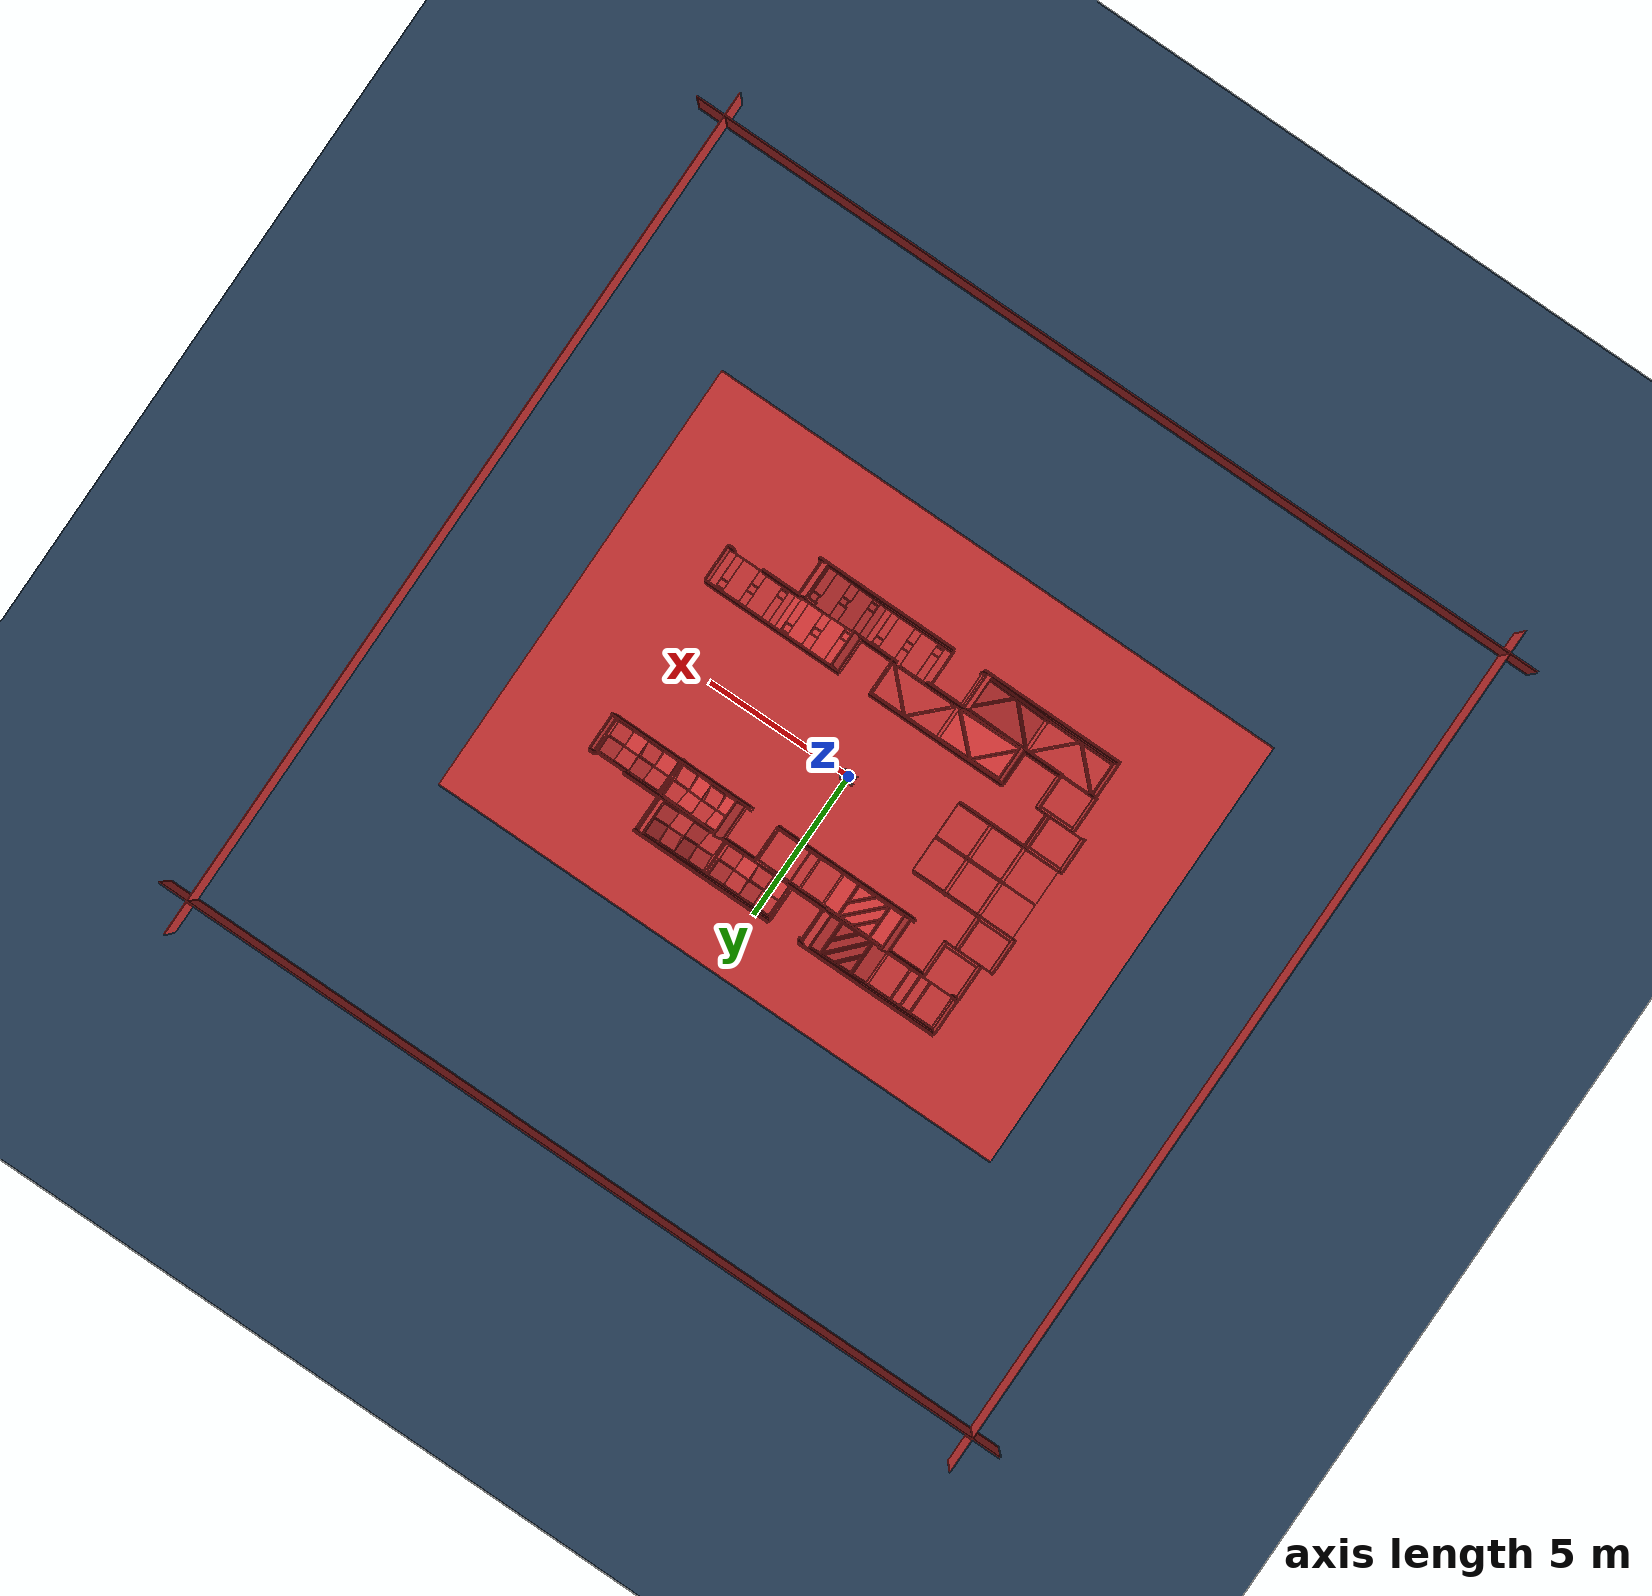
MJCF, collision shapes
<mujoco model="go2 scene">
  <include file="go2.xml" />
  <statistic center="0 0 0.1" extent="0.8" />

  <visual>
    <headlight diffuse="0.6 0.6 0.6" ambient="0.3 0.3 0.3" specular="0 0 0" />
    <rgba haze="0.15 0.25 0.35 1" />
    <global azimuth="-130" elevation="-20" />
    <map znear="0.01" zfar="100"/>
  </visual>

  <asset>
    <texture type="skybox" builtin="gradient" rgb1="0.3 0.5 0.7" rgb2="0 0 0" width="512" height="3072" />
    <texture type="2d" name="groundplane" builtin="checker" mark="edge" rgb1="0.2 0.3 0.4" rgb2="0.1 0.2 0.3" markrgb="0.8 0.8 0.8" width="300" height="300" />
    <material name="groundplane" texture="groundplane" texuniform="true" texrepeat="5 5" reflectance="0.2" />
  <hfield name="perlin_hfield" size="1.0 0.75 0.2 0.2" file="../height_field.png" /><hfield name="image_hfield" size="1.0 1.0 0.02 0.1" file="../unitree_hfield.png" /></asset>

  <worldbody>
    <light pos="0 0 1.5" dir="0 0 -1" directional="true" />
    <geom name="floor" pos="0 0.0 0.001" size="0 0 0.05" type="plane" material="groundplane" />
<geom name="phs_Cube" type="box" size="10.0 7.5 0.5" pos="0.0 -0.4 -0.484" quat="1.0 0.0 0.0 0.0" rgba="0.8 0.2 0.2 1" solref="0.02 1" solimp="0.9 0.95 0.001"/>
<geom name="phs_Cube2" type="box" size="0.125 0.6 0.1" pos="6.63 -3.01 0.025" quat="1.0 0.0 0.0 0.0" rgba="0.8 0.2 0.2 1" solref="0.02 1" solimp="0.9 0.95 0.001"/>
<geom name="phs_Cube3" type="box" size="0.29 0.6 0.1" pos="5.96 -3.01 0.025" quat="1.0 0.0 0.0 0.0" rgba="0.8 0.2 0.2 1" solref="0.02 1" solimp="0.9 0.95 0.001"/>
<geom name="phs_Cube4" type="box" size="0.29 0.6 0.1" pos="5.13 -3.01 0.025" quat="1.0 0.0 0.0 0.0" rgba="0.8 0.2 0.2 1" solref="0.02 1" solimp="0.9 0.95 0.001"/>
<geom name="phs_Cube5" type="box" size="0.11 0.6 0.1" pos="4.48 -3.01 0.025" quat="1.0 0.0 0.0 0.0" rgba="0.8 0.2 0.2 1" solref="0.02 1" solimp="0.9 0.95 0.001"/>
<geom name="phs_Cube11" type="box" size="0.29 0.6 0.1" pos="1.16 -4.21 0.025" quat="1.0 0.0 0.0 0.0" rgba="0.8 0.2 0.2 1" solref="0.02 1" solimp="0.9 0.95 0.001"/>
<geom name="phs_Cube12" type="box" size="0.29 0.6 0.1" pos="0.34 -4.21 0.025" quat="1.0 0.0 0.0 0.0" rgba="0.8 0.2 0.2 1" solref="0.02 1" solimp="0.9 0.95 0.001"/>
<geom name="phs_Cube24" type="box" size="0.125 0.435 0.1" pos="4.715 -2.83 0.025" quat="1.0 0.0 0.0 0.0" rgba="0.8 0.2 0.2 1" solref="0.02 1" solimp="0.9 0.95 0.001"/>
<geom name="phs_Cube25" type="box" size="0.1265 0.42 0.1" pos="6.377 -3.19 0.025" quat="1.0 0.0 0.0 0.0" rgba="0.8 0.2 0.2 1" solref="0.02 1" solimp="0.9 0.95 0.001"/>
<geom name="phs_Cube26" type="box" size="0.1265 0.06 0.1" pos="6.377 -2.455 0.0251" quat="1.0 0.0 0.0 0.0" rgba="0.8 0.2 0.2 1" solref="0.02 1" solimp="0.9 0.95 0.001"/>
<geom name="phs_Cube27" type="box" size="0.1265 0.235 0.1" pos="5.543 -3.374 0.0251" quat="1.0 0.0 0.0 0.0" rgba="0.8 0.2 0.2 1" solref="0.02 1" solimp="0.9 0.95 0.001"/>
<geom name="phs_Cube28" type="box" size="0.1265 0.24 0.1" pos="5.543 -2.648 0.0251" quat="1.0 0.0 0.0 0.0" rgba="0.8 0.2 0.2 1" solref="0.02 1" solimp="0.9 0.95 0.001"/>
<geom name="phs_Cube29" type="box" size="0.125 0.05 0.1" pos="4.715 -3.56 0.0251" quat="1.0 0.0 0.0 0.0" rgba="0.8 0.2 0.2 1" solref="0.02 1" solimp="0.9 0.95 0.001"/>
<geom name="phs_Cube30" type="box" size="0.125 0.425 0.1" pos="1.575 -4.39 0.025" quat="1.0 0.0 0.0 0.0" rgba="0.8 0.2 0.2 1" solref="0.02 1" solimp="0.9 0.95 0.001"/>
<geom name="phs_Cube31" type="box" size="0.125 0.055 0.1" pos="1.575 -3.663 0.0251" quat="1.0 0.0 0.0 0.0" rgba="0.8 0.2 0.2 1" solref="0.02 1" solimp="0.9 0.95 0.001"/>
<geom name="phs_Cube32" type="box" size="0.125 0.235 0.1" pos="0.75 -4.581 0.0251" quat="1.0 0.0 0.0 0.0" rgba="0.8 0.2 0.2 1" solref="0.02 1" solimp="0.9 0.95 0.001"/>
<geom name="phs_Cube33" type="box" size="0.125 0.265 0.1" pos="0.75 -3.828 0.0251" quat="1.0 0.0 0.0 0.0" rgba="0.8 0.2 0.2 1" solref="0.02 1" solimp="0.9 0.95 0.001"/>
<geom name="phs_Cube34" type="box" size="0.125 0.6 0.1" pos="-0.33 -4.21 0.025" quat="1.0 0.0 0.0 0.0" rgba="0.8 0.2 0.2 1" solref="0.02 1" solimp="0.9 0.95 0.001"/>
<geom name="phs_Cube35" type="box" size="0.126 0.425 0.1" pos="-0.0775 -4.037 0.025" quat="1.0 0.0 0.0 0.0" rgba="0.8 0.2 0.2 1" solref="0.02 1" solimp="0.9 0.95 0.001"/>
<geom name="phs_Cube36" type="box" size="0.126 0.05 0.1" pos="-0.0775 -4.77 0.0251" quat="1.0 0.0 0.0 0.0" rgba="0.8 0.2 0.2 1" solref="0.02 1" solimp="0.9 0.95 0.001"/>
<geom name="phs_Cube37" type="box" size="3.75 0.044 0.1" pos="-2.61 -3.607 0.0095" quat="1.0 0.0 0.0 0.0" rgba="0.8 0.2 0.2 1" solref="0.02 1" solimp="0.9 0.95 0.001"/>
<geom name="phs_Cube38" type="box" size="1.25 0.044 0.1" pos="-0.35 -2.43 0.0095" quat="1.0 0.0 0.0 0.0" rgba="0.8 0.2 0.2 1" solref="0.02 1" solimp="0.9 0.95 0.001"/>
<geom name="phs_Cube39" type="box" size="0.55 0.044 0.1" pos="0.872 -3.02 0.0095" quat="0.707107 0.0 0.0 -0.707107" rgba="0.8 0.2 0.2 1" solref="0.02 1" solimp="0.9 0.95 0.001"/>
<geom name="phs_Cube40" type="box" size="0.55 0.055 0.1" pos="-1.525 -3.02 0.0095" quat="0.707107 0.0 0.0 -0.707107" rgba="0.8 0.2 0.2 1" solref="0.02 1" solimp="0.9 0.95 0.001"/>
<geom name="phs_Cube41" type="box" size="0.6 0.055 0.1" pos="-3.81 -3.02 0.7095" quat="0.700225 -0.09841 0.09841 -0.700225" rgba="0.8 0.2 0.2 1" solref="0.02 1" solimp="0.9 0.95 0.001"/>
<geom name="phs_Cube42" type="box" size="0.56 0.055 0.1" pos="-3.93 -4.21 0.0095" quat="0.707107 0.0 0.0 -0.707107" rgba="0.8 0.2 0.2 1" solref="0.02 1" solimp="0.9 0.95 0.001"/>
<geom name="phs_Cube43" type="box" size="0.56 0.055 0.1" pos="-6.33 -4.21 0.0095" quat="0.707107 0.0 0.0 -0.707107" rgba="0.8 0.2 0.2 1" solref="0.02 1" solimp="0.9 0.95 0.001"/>
<geom name="phs_Cube45" type="box" size="0.85 0.03 0.1" pos="-4.53 -4.19 0.0095" quat="0.92388 0.0 0.0 0.382683" rgba="0.8 0.2 0.2 1" solref="0.02 1" solimp="0.9 0.95 0.001"/>
<geom name="phs_Cube46" type="box" size="0.85 0.03 0.1" pos="-5.73 -4.19 0.0095" quat="0.92388 0.0 0.0 -0.382683" rgba="0.8 0.2 0.2 1" solref="0.02 1" solimp="0.9 0.95 0.001"/>
<geom name="phs_Cube47" type="box" size="2.425 0.044 0.1" pos="-3.91 -4.81 0.0095" quat="1.0 0.0 0.0 0.0" rgba="0.8 0.2 0.2 1" solref="0.02 1" solimp="0.9 0.95 0.001"/>
<geom name="phs_Cube50" type="box" size="0.6 0.6 0.1" pos="-5.76 -3.01 0.12" quat="1.0 0.0 0.0 0.0" rgba="0.8 0.2 0.2 1" solref="0.02 1" solimp="0.9 0.95 0.001"/>
<geom name="phs_Cube51" type="box" size="0.65 0.6 0.1" pos="-6.12 -1.805 0.12" quat="1.0 0.0 0.0 0.0" rgba="0.8 0.2 0.2 1" solref="0.02 1" solimp="0.9 0.95 0.001"/>
<geom name="phs_Cube52" type="box" size="1.8 0.6 0.1" pos="-4.943 -0.605 0.12" quat="1.0 0.0 0.0 0.0" rgba="0.8 0.2 0.2 1" solref="0.02 1" solimp="0.9 0.95 0.001"/>
<geom name="phs_Cube53" type="box" size="1.8 0.6 0.1" pos="-4.943 0.603 0.12" quat="1.0 0.0 0.0 0.0" rgba="0.8 0.2 0.2 1" solref="0.02 1" solimp="0.9 0.95 0.001"/>
<geom name="phs_Cube54" type="box" size="0.625 0.6 0.1" pos="-6.16 1.81 0.12" quat="1.0 0.0 0.0 0.0" rgba="0.8 0.2 0.2 1" solref="0.02 1" solimp="0.9 0.95 0.001"/>
<geom name="phs_Cube55" type="box" size="0.6 0.6 0.1" pos="-5.75 3.06 0.12" quat="1.0 0.0 0.0 0.0" rgba="0.8 0.2 0.2 1" solref="0.02 1" solimp="0.9 0.95 0.001"/>
<geom name="phs_Cube56" type="box" size="0.6 0.05 0.1" pos="-6.16 -1.265 0.27" quat="1.0 0.0 0.0 0.0" rgba="0.8 0.2 0.2 1" solref="0.02 1" solimp="0.9 0.95 0.001"/>
<geom name="phs_Cube57" type="box" size="0.6 0.05 0.1" pos="-5.76 -2.465 0.27" quat="1.0 0.0 0.0 0.0" rgba="0.8 0.2 0.2 1" solref="0.02 1" solimp="0.9 0.95 0.001"/>
<geom name="phs_Cube58" type="box" size="0.6 0.05 0.1" pos="-6.16 1.26 0.27" quat="1.0 0.0 0.0 0.0" rgba="0.8 0.2 0.2 1" solref="0.02 1" solimp="0.9 0.95 0.001"/>
<geom name="phs_Cube59" type="box" size="0.6 0.05 0.1" pos="-5.76 2.46 0.27" quat="1.0 0.0 0.0 0.0" rgba="0.8 0.2 0.2 1" solref="0.02 1" solimp="0.9 0.95 0.001"/>
<geom name="phs_Cube60" type="box" size="1.25 0.05 0.1" pos="-5.51 0.02 0.27" quat="0.707107 0.0 0.0 -0.707107" rgba="0.8 0.2 0.2 1" solref="0.02 1" solimp="0.9 0.95 0.001"/>
<geom name="phs_Cube61" type="box" size="1.25 0.05 0.1" pos="-4.31 0.02 0.27" quat="0.707107 0.0 0.0 -0.707107" rgba="0.8 0.2 0.2 1" solref="0.02 1" solimp="0.9 0.95 0.001"/>
<geom name="phs_Cube62" type="box" size="0.05 0.6 0.1" pos="-6.315 4.22 0.01" quat="1.0 0.0 0.0 0.0" rgba="0.8 0.2 0.2 1" solref="0.02 1" solimp="0.9 0.95 0.001"/>
<geom name="phs_Cube63" type="box" size="0.055 0.6 0.1" pos="-1.63 4.23 0.7" quat="0.989016 0.0 -0.147809 0.0" rgba="0.8 0.2 0.2 1" solref="0.02 1" solimp="0.9 0.95 0.001"/>
<geom name="phs_Cube64" type="box" size="0.025 0.6 0.1" pos="-5.477 4.22 0.058" quat="1.0 0.0 0.0 0.0" rgba="0.8 0.2 0.2 1" solref="0.02 1" solimp="0.9 0.95 0.001"/>
<geom name="phs_Cube65" type="box" size="0.025 0.6 0.1" pos="-5.12 4.22 0.058" quat="1.0 0.0 0.0 0.0" rgba="0.8 0.2 0.2 1" solref="0.02 1" solimp="0.9 0.95 0.001"/>
<geom name="phs_Cube66" type="box" size="0.025 0.6 0.1" pos="-4.77 4.22 0.058" quat="1.0 0.0 0.0 0.0" rgba="0.8 0.2 0.2 1" solref="0.02 1" solimp="0.9 0.95 0.001"/>
<geom name="phs_Cube67" type="box" size="0.035 0.6 0.1" pos="-3.93 4.21 0.02" quat="1.0 0.0 0.0 0.0" rgba="0.8 0.2 0.2 1" solref="0.02 1" solimp="0.9 0.95 0.001"/>
<geom name="phs_Cube70" type="box" size="0.05 4.5 0.1" pos="-0.125 3.61 0.01" quat="0.707107 0.0 0.0 0.707107" rgba="0.8 0.2 0.2 1" solref="0.02 1" solimp="0.9 0.95 0.001"/>
<geom name="phs_Cube71" type="box" size="0.05 0.3 0.1" pos="-4.87 3.607 0.058" quat="0.707107 0.0 0.0 0.707107" rgba="0.8 0.2 0.2 1" solref="0.02 1" solimp="0.9 0.95 0.001"/>
<geom name="phs_Cube72" type="box" size="0.05 2.4 0.1" pos="-3.87 4.82 0.01" quat="0.707107 0.0 0.0 -0.707107" rgba="0.8 0.2 0.2 1" solref="0.02 1" solimp="0.9 0.95 0.001"/>
<geom name="phs_Cube73" type="box" size="0.05 0.55 0.1" pos="-5.12 4.82 0.058" quat="0.707107 0.0 0.0 -0.707107" rgba="0.8 0.2 0.2 1" solref="0.02 1" solimp="0.9 0.95 0.001"/>
<geom name="phs_Cube74" type="box" size="0.05 0.55 0.1" pos="-2.81 4.82 0.388" quat="0.69934 0.104517 -0.104517 -0.69934" rgba="0.8 0.2 0.2 1" solref="0.02 1" solimp="0.9 0.95 0.001"/>
<geom name="phs_Cube76" type="box" size="0.05 0.55 0.1" pos="-2.72 2.42 0.12" quat="0.707107 0.0 0.0 -0.707107" rgba="0.8 0.2 0.2 1" solref="0.02 1" solimp="0.9 0.95 0.001"/>
<geom name="phs_Cube77" type="box" size="0.05 2.4 0.1" pos="-1.525 2.41 0.01" quat="0.707107 0.0 0.0 0.707107" rgba="0.8 0.2 0.2 1" solref="0.02 1" solimp="0.9 0.95 0.001"/>
<geom name="phs_Cube78" type="box" size="0.05 0.55 0.1" pos="-0.32 2.42 0.058" quat="0.707107 0.0 0.0 -0.707107" rgba="0.8 0.2 0.2 1" solref="0.02 1" solimp="0.9 0.95 0.001"/>
<geom name="phs_Cube79" type="box" size="0.025 0.55 0.1" pos="-0.32 3.59 0.058" quat="0.707107 0.0 0.0 -0.707107" rgba="0.8 0.2 0.2 1" solref="0.02 1" solimp="0.9 0.95 0.001"/>
<geom name="phs_Cube80" type="box" size="0.055 0.6 0.1" pos="0.88 3.03 0.01" quat="1.0 0.0 0.0 0.0" rgba="0.8 0.2 0.2 1" solref="0.02 1" solimp="0.9 0.95 0.001"/>
<geom name="phs_Cube81" type="box" size="0.025 0.6 0.1" pos="1.93 4.19 0.02" quat="1.0 0.0 0.0 0.0" rgba="0.8 0.2 0.2 1" solref="0.02 1" solimp="0.9 0.95 0.001"/>
<geom name="phs_Cube82" type="box" size="0.055 1.25 0.1" pos="4.35 3.59 0.01" quat="1.0 0.0 0.0 0.0" rgba="0.8 0.2 0.2 1" solref="0.02 1" solimp="0.9 0.95 0.001"/>
<geom name="phs_Cube83" type="box" size="0.055 0.6 0.1" pos="6.75 2.99 0.01" quat="1.0 0.0 0.0 0.0" rgba="0.8 0.2 0.2 1" solref="0.02 1" solimp="0.9 0.95 0.001"/>
<geom name="phs_Cube84" type="box" size="0.025 1.25 0.1" pos="5.56 3.61 0.01" quat="0.707107 0.0 0.0 0.707107" rgba="0.8 0.2 0.2 1" solref="0.02 1" solimp="0.9 0.95 0.001"/>
<geom name="phs_Cube85" type="box" size="0.05 2.5 0.1" pos="4.31 2.42 0.01" quat="0.707107 0.0 0.0 0.707107" rgba="0.8 0.2 0.2 1" solref="0.02 1" solimp="0.9 0.95 0.001"/>
<geom name="phs_Cube89" type="box" size="0.025 0.8 0.1" pos="-2.805 4.21 0.395" quat="0.91166 0.045729 -0.156247 -0.377323" rgba="0.8 0.2 0.2 1" solref="0.02 1" solimp="0.9 0.95 0.001"/>
<geom name="phs_Cube90" type="box" size="0.025 0.45 0.1" pos="-3.05 4.45 0.318" quat="0.91176 0.051459 -0.153961 -0.377283" rgba="0.8 0.2 0.2 1" solref="0.02 1" solimp="0.9 0.95 0.001"/>
<geom name="phs_Cube91" type="box" size="0.025 0.45 0.1" pos="-2.57 3.96 0.465" quat="0.91166 0.045729 -0.156247 -0.377323" rgba="0.8 0.2 0.2 1" solref="0.02 1" solimp="0.9 0.95 0.001"/>
<geom name="phs_Cube92" type="box" size="0.03 0.6 0.1" pos="-0.67 3.03 0.058" quat="1.0 0.0 0.0 0.0" rgba="0.8 0.2 0.2 1" solref="0.02 1" solimp="0.9 0.95 0.001"/>
<geom name="phs_Cube93" type="box" size="0.02 0.6 0.1" pos="-0.32 3.03 0.058" quat="1.0 0.0 0.0 0.0" rgba="0.8 0.2 0.2 1" solref="0.02 1" solimp="0.9 0.95 0.001"/>
<geom name="phs_Cube94" type="box" size="0.03 0.6 0.1" pos="0.02 3.02 0.058" quat="1.0 0.0 0.0 0.0" rgba="0.8 0.2 0.2 1" solref="0.02 1" solimp="0.9 0.95 0.001"/>
<geom name="phs_Cube95" type="box" size="0.055 0.6 0.1" pos="-0.45 4.24 0.01" quat="1.0 0.0 0.0 0.0" rgba="0.8 0.2 0.2 1" solref="0.02 1" solimp="0.9 0.95 0.001"/>
<geom name="phs_Cube96" type="box" size="0.05 2.4 0.1" pos="1.975 4.81 0.01" quat="0.707107 0.0 0.0 0.707107" rgba="0.8 0.2 0.2 1" solref="0.02 1" solimp="0.9 0.95 0.001"/>
<geom name="phs_Cube97" type="box" size="0.275 0.275 0.1" pos="1.53 3.91 0.02" quat="0.990268 -0.139173 0.0 0.0" rgba="0.8 0.2 0.2 1" solref="0.02 1" solimp="0.9 0.95 0.001"/>
<geom name="phs_Cube98" type="box" size="0.275 0.275 0.1" pos="1.56 4.49 0.02" quat="0.990268 0.0 -0.139173 0.0" rgba="0.8 0.2 0.2 1" solref="0.02 1" solimp="0.9 0.95 0.001"/>
<geom name="phs_Cube99" type="box" size="0.275 0.275 0.1" pos="0.99 4.51 0.02" quat="0.990268 0.139173 0.0 0.0" rgba="0.8 0.2 0.2 1" solref="0.02 1" solimp="0.9 0.95 0.001"/>
<geom name="phs_Cube100" type="box" size="0.275 0.275 0.1" pos="0.97 3.94 0.02" quat="0.990268 0.0 0.139173 0.0" rgba="0.8 0.2 0.2 1" solref="0.02 1" solimp="0.9 0.95 0.001"/>
<geom name="phs_Cube101" type="box" size="0.275 0.275 0.1" pos="0.48 4.49 0.02" quat="0.990268 0.0 -0.139173 0.0" rgba="0.8 0.2 0.2 1" solref="0.02 1" solimp="0.9 0.95 0.001"/>
<geom name="phs_Cube102" type="box" size="0.275 0.275 0.1" pos="-0.07 4.51 0.02" quat="0.990268 0.139173 0.0 0.0" rgba="0.8 0.2 0.2 1" solref="0.02 1" solimp="0.9 0.95 0.001"/>
<geom name="phs_Cube103" type="box" size="0.275 0.275 0.1" pos="0.46 3.91 0.02" quat="0.990268 -0.139173 0.0 0.0" rgba="0.8 0.2 0.2 1" solref="0.02 1" solimp="0.9 0.95 0.001"/>
<geom name="phs_Cube104" type="box" size="0.275 0.275 0.1" pos="-0.12 3.94 0.02" quat="0.990268 0.0 0.139173 0.0" rgba="0.8 0.2 0.2 1" solref="0.02 1" solimp="0.9 0.95 0.001"/>
<geom name="phs_Cube105" type="box" size="0.275 0.275 0.1" pos="3.84 3.92 0.59" quat="0.980631 -0.137819 -0.137819 -0.019369" rgba="0.8 0.2 0.2 1" solref="0.02 1" solimp="0.9 0.95 0.001"/>
<geom name="phs_Cube106" type="box" size="0.275 0.275 0.1" pos="3.86 4.49 0.592" quat="0.96005 0.0 -0.279829 0.0" rgba="0.8 0.2 0.2 1" solref="0.02 1" solimp="0.9 0.95 0.001"/>
<geom name="phs_Cube107" type="box" size="0.275 0.275 0.1" pos="3.325 4.51 0.43" quat="0.979391 0.137644 -0.146371 0.020571" rgba="0.8 0.2 0.2 1" solref="0.02 1" solimp="0.9 0.95 0.001"/>
<geom name="phs_Cube108" type="box" size="0.275 0.275 0.1" pos="3.31 3.94 0.43" quat="0.999962 0.0 -0.008727 0.0" rgba="0.8 0.2 0.2 1" solref="0.02 1" solimp="0.9 0.95 0.001"/>
<geom name="phs_Cube109" type="box" size="0.275 0.275 0.1" pos="2.84 4.49 0.293" quat="0.961262 0.0 -0.275637 0.0" rgba="0.8 0.2 0.2 1" solref="0.02 1" solimp="0.9 0.95 0.001"/>
<geom name="phs_Cube110" type="box" size="0.275 0.275 0.1" pos="2.31 4.52 0.125" quat="0.979391 0.137644 -0.146371 0.020571" rgba="0.8 0.2 0.2 1" solref="0.02 1" solimp="0.9 0.95 0.001"/>
<geom name="phs_Cube111" type="box" size="0.275 0.275 0.1" pos="2.8 3.91 0.27" quat="0.979391 -0.137644 -0.146371 -0.020571" rgba="0.8 0.2 0.2 1" solref="0.02 1" solimp="0.9 0.95 0.001"/>
<geom name="phs_Cube112" type="box" size="0.275 0.275 0.1" pos="2.28 3.94 0.115" quat="0.999914 0.0 -0.01309 0.0" rgba="0.8 0.2 0.2 1" solref="0.02 1" solimp="0.9 0.95 0.001"/>
<geom name="phs_Cube113" type="box" size="0.275 0.275 0.1" pos="3.96 2.71 0.14" quat="0.979391 -0.137644 0.146371 0.020571" rgba="0.8 0.2 0.2 1" solref="0.02 1" solimp="0.9 0.95 0.001"/>
<geom name="phs_Cube114" type="box" size="0.275 0.275 0.1" pos="3.97 3.29 0.125" quat="0.999962 0.0 0.008727 0.0" rgba="0.8 0.2 0.2 1" solref="0.02 1" solimp="0.9 0.95 0.001"/>
<geom name="phs_Cube115" type="box" size="0.275 0.275 0.1" pos="3.45 3.308 0.288" quat="0.979391 0.137644 0.146371 -0.020571" rgba="0.8 0.2 0.2 1" solref="0.02 1" solimp="0.9 0.95 0.001"/>
<geom name="phs_Cube116" type="box" size="0.275 0.275 0.1" pos="3.41 2.74 0.302" quat="0.961262 0.0 0.275637 0.0" rgba="0.8 0.2 0.2 1" solref="0.02 1" solimp="0.9 0.95 0.001"/>
<geom name="phs_Cube117" type="box" size="0.275 0.275 0.1" pos="2.95 3.29 0.437" quat="0.999848 0.0 0.017452 0.0" rgba="0.8 0.2 0.2 1" solref="0.02 1" solimp="0.9 0.95 0.001"/>
<geom name="phs_Cube118" type="box" size="0.275 0.275 0.1" pos="2.42 3.3 0.6" quat="0.979391 0.137644 0.146371 -0.020571" rgba="0.8 0.2 0.2 1" solref="0.02 1" solimp="0.9 0.95 0.001"/>
<geom name="phs_Cube119" type="box" size="0.275 0.275 0.1" pos="2.93 2.73 0.44" quat="0.979391 -0.137644 0.146371 0.020571" rgba="0.8 0.2 0.2 1" solref="0.02 1" solimp="0.9 0.95 0.001"/>
<geom name="phs_Cube120" type="box" size="0.275 0.275 0.1" pos="2.41 2.73 0.6" quat="0.95882 0.0 0.284015 0.0" rgba="0.8 0.2 0.2 1" solref="0.02 1" solimp="0.9 0.95 0.001"/>
<geom name="phs_Cube121" type="box" size="0.275 0.275 0.1" pos="6.33 2.71 0.02" quat="0.990268 -0.139173 0.0 0.0" rgba="0.8 0.2 0.2 1" solref="0.02 1" solimp="0.9 0.95 0.001"/>
<geom name="phs_Cube122" type="box" size="0.275 0.275 0.1" pos="6.36 3.29 0.02" quat="0.990268 0.0 -0.139173 0.0" rgba="0.8 0.2 0.2 1" solref="0.02 1" solimp="0.9 0.95 0.001"/>
<geom name="phs_Cube123" type="box" size="0.275 0.275 0.1" pos="5.79 3.31 0.02" quat="0.990268 0.139173 0.0 0.0" rgba="0.8 0.2 0.2 1" solref="0.02 1" solimp="0.9 0.95 0.001"/>
<geom name="phs_Cube124" type="box" size="0.275 0.275 0.1" pos="5.77 2.74 0.02" quat="0.990268 0.0 0.139173 0.0" rgba="0.8 0.2 0.2 1" solref="0.02 1" solimp="0.9 0.95 0.001"/>
<geom name="phs_Cube125" type="box" size="0.275 0.275 0.1" pos="5.28 3.29 0.02" quat="0.990268 0.0 -0.139173 0.0" rgba="0.8 0.2 0.2 1" solref="0.02 1" solimp="0.9 0.95 0.001"/>
<geom name="phs_Cube126" type="box" size="0.275 0.275 0.1" pos="4.73 3.31 0.02" quat="0.990268 0.139173 0.0 0.0" rgba="0.8 0.2 0.2 1" solref="0.02 1" solimp="0.9 0.95 0.001"/>
<geom name="phs_Cube127" type="box" size="0.275 0.275 0.1" pos="5.26 2.71 0.02" quat="0.990268 -0.139173 0.0 0.0" rgba="0.8 0.2 0.2 1" solref="0.02 1" solimp="0.9 0.95 0.001"/>
<geom name="phs_Cube128" type="box" size="0.275 0.275 0.1" pos="4.68 2.74 0.02" quat="0.990268 0.0 0.139173 0.0" rgba="0.8 0.2 0.2 1" solref="0.02 1" solimp="0.9 0.95 0.001"/>
<geom name="phs_Cube129" type="box" size="0.85 0.025 0.1" pos="-3.17 -2.97 0.51" quat="0.918422 0.048248 0.132605 0.369579" rgba="0.8 0.2 0.2 1" solref="0.02 1" solimp="0.9 0.95 0.001"/>
<geom name="phs_Cube130" type="box" size="0.85 0.025 0.1" pos="-2.11 -3.0 0.19" quat="0.910754 0.127882 0.059649 -0.388091" rgba="0.8 0.2 0.2 1" solref="0.02 1" solimp="0.9 0.95 0.001"/>
<geom name="phs_Cube131" type="box" size="0.85 0.03 0.1" pos="-0.87 -2.99 0.0095" quat="0.92388 0.0 0.0 0.382683" rgba="0.8 0.2 0.2 1" solref="0.02 1" solimp="0.9 0.95 0.001"/>
<geom name="phs_Cube132" type="box" size="0.85 0.03 0.1" pos="0.22 -2.99 0.0095" quat="0.92388 0.0 0.0 -0.382683" rgba="0.8 0.2 0.2 1" solref="0.02 1" solimp="0.9 0.95 0.001"/>
<geom name="phs_Cube133" type="box" size="0.025 0.6 0.5" pos="6.77 -3.01 0.5" quat="1.0 0.0 0.0 0.0" rgba="0.8 0.2 0.2 1" solref="0.02 1" solimp="0.9 0.95 0.001"/>
<geom name="phs_Cube134" type="box" size="0.025 0.6 0.5" pos="2.12 -3.01 0.97" quat="0.989016 0.0 0.147809 0.0" rgba="0.8 0.2 0.2 1" solref="0.02 1" solimp="0.9 0.95 0.001"/>
<geom name="phs_Cube135" type="box" size="0.025 0.6 0.5" pos="0.88 -3.01 0.5" quat="1.0 0.0 0.0 0.0" rgba="0.8 0.2 0.2 1" solref="0.02 1" solimp="0.9 0.95 0.001"/>
<geom name="phs_Cube136" type="box" size="0.025 0.6 0.5" pos="-3.785 -3.01 0.8" quat="0.990268 0.0 0.139173 0.0" rgba="0.8 0.2 0.2 1" solref="0.02 1" solimp="0.9 0.95 0.001"/>
<geom name="phs_Cube137" type="box" size="0.025 0.6 0.5" pos="-5.14 -3.01 0.5" quat="1.0 0.0 0.0 0.0" rgba="0.8 0.2 0.2 1" solref="0.02 1" solimp="0.9 0.95 0.001"/>
<geom name="phs_Cube138" type="box" size="0.025 0.6 0.5" pos="-6.38 -3.01 0.5" quat="1.0 0.0 0.0 0.0" rgba="0.8 0.2 0.2 1" solref="0.02 1" solimp="0.9 0.95 0.001"/>
<geom name="phs_Cube139" type="box" size="0.025 0.6 0.5" pos="-6.34 -4.21 0.5" quat="1.0 0.0 0.0 0.0" rgba="0.8 0.2 0.2 1" solref="0.02 1" solimp="0.9 0.95 0.001"/>
<geom name="phs_Cube140" type="box" size="0.01 0.6 0.5" pos="-1.67 -4.21 0.89" quat="0.990268 0.0 -0.139173 0.0" rgba="0.8 0.2 0.2 1" solref="0.02 1" solimp="0.9 0.95 0.001"/>
<geom name="phs_Cube141" type="box" size="0.025 0.6 0.5" pos="-0.47 -4.21 0.5" quat="1.0 0.0 0.0 0.0" rgba="0.8 0.2 0.2 1" solref="0.02 1" solimp="0.9 0.95 0.001"/>
<geom name="phs_Cube143" type="box" size="0.025 0.675 0.5" pos="1.41 -3.6 0.5" quat="0.707107 0.0 0.0 -0.707107" rgba="0.8 0.2 0.2 1" solref="0.02 1" solimp="0.9 0.95 0.001"/>
<geom name="phs_Cube144" type="box" size="0.03 0.675 0.5" pos="-0.99 -3.61 0.5" quat="0.707107 0.0 0.0 -0.707107" rgba="0.8 0.2 0.2 1" solref="0.02 1" solimp="0.9 0.95 0.001"/>
<geom name="phs_Cube145" type="box" size="0.025 0.69 0.5" pos="-4.47 -3.6 0.5" quat="0.707107 0.0 0.0 -0.707107" rgba="0.8 0.2 0.2 1" solref="0.02 1" solimp="0.9 0.95 0.001"/>
<geom name="phs_Cube146" type="box" size="0.01 0.075 0.5" pos="-6.25 -3.62 0.5" quat="0.707107 0.0 0.0 -0.707107" rgba="0.8 0.2 0.2 1" solref="0.02 1" solimp="0.9 0.95 0.001"/>
<geom name="phs_Cube147" type="box" size="0.025 2.4 0.75" pos="-3.92 -4.83 0.5" quat="0.707107 0.0 0.0 -0.707107" rgba="0.8 0.2 0.2 1" solref="0.02 1" solimp="0.9 0.95 0.001"/>
<geom name="phs_Cube148" type="box" size="0.025 2.4 0.75" pos="1.95 -4.83 0.5" quat="0.707107 0.0 0.0 -0.707107" rgba="0.8 0.2 0.2 1" solref="0.02 1" solimp="0.9 0.95 0.001"/>
<geom name="phs_Cube149" type="box" size="0.025 2.4 0.5" pos="-1.51 -2.39 0.5" quat="0.707107 0.0 0.0 -0.707107" rgba="0.8 0.2 0.2 1" solref="0.02 1" solimp="0.9 0.95 0.001"/>
<geom name="phs_Cube150" type="box" size="0.025 2.4 0.5" pos="4.37 -2.39 0.5" quat="0.707107 0.0 0.0 -0.707107" rgba="0.8 0.2 0.2 1" solref="0.02 1" solimp="0.9 0.95 0.001"/>
<geom name="phs_Cube151" type="box" size="0.025 0.67 0.5" pos="4.88 -3.61 0.5" quat="0.707107 0.0 0.0 -0.707107" rgba="0.8 0.2 0.2 1" solref="0.02 1" solimp="0.9 0.95 0.001"/>
<geom name="phs_Cube152" type="box" size="0.025 0.1 0.5" pos="6.68 -3.63 0.5" quat="0.707107 0.0 0.0 -0.707107" rgba="0.8 0.2 0.2 1" solref="0.02 1" solimp="0.9 0.95 0.001"/>
<geom name="phs_Cube153" type="box" size="0.025 0.6 0.5" pos="-6.77 -1.81 0.5" quat="1.0 0.0 0.0 0.0" rgba="0.8 0.2 0.2 1" solref="0.02 1" solimp="0.9 0.95 0.001"/>
<geom name="phs_Cube154" type="box" size="0.025 0.6 0.5" pos="-5.53 -1.81 0.5" quat="1.0 0.0 0.0 0.0" rgba="0.8 0.2 0.2 1" solref="0.02 1" solimp="0.9 0.95 0.001"/>
<geom name="phs_Cube155" type="box" size="0.025 0.6 0.5" pos="-6.76 1.81 0.5" quat="1.0 0.0 0.0 0.0" rgba="0.8 0.2 0.2 1" solref="0.02 1" solimp="0.9 0.95 0.001"/>
<geom name="phs_Cube156" type="box" size="0.025 0.6 0.5" pos="-5.53 1.79 0.5" quat="1.0 0.0 0.0 0.0" rgba="0.8 0.2 0.2 1" solref="0.02 1" solimp="0.9 0.95 0.001"/>
<geom name="phs_Cube157" type="box" size="0.025 0.6 0.5" pos="-6.37 3.01 0.5" quat="1.0 0.0 0.0 0.0" rgba="0.8 0.2 0.2 1" solref="0.02 1" solimp="0.9 0.95 0.001"/>
<geom name="phs_Cube158" type="box" size="0.025 0.6 0.5" pos="-5.14 3.0 0.5" quat="1.0 0.0 0.0 0.0" rgba="0.8 0.2 0.2 1" solref="0.02 1" solimp="0.9 0.95 0.001"/>
<geom name="phs_Cube159" type="box" size="0.025 1.2 0.5" pos="-4.35 -1.24 0.5" quat="0.707107 0.0 0.0 -0.707107" rgba="0.8 0.2 0.2 1" solref="0.02 1" solimp="0.9 0.95 0.001"/>
<geom name="phs_Cube160" type="box" size="0.025 1.2 0.5" pos="-4.35 0.0 0.5" quat="0.707107 0.0 0.0 -0.707107" rgba="0.8 0.2 0.2 1" solref="0.02 1" solimp="0.9 0.95 0.001"/>
<geom name="phs_Cube161" type="box" size="0.025 1.2 0.5" pos="-4.35 1.22 0.5" quat="0.707107 0.0 0.0 -0.707107" rgba="0.8 0.2 0.2 1" solref="0.02 1" solimp="0.9 0.95 0.001"/>
<geom name="phs_Cube162" type="box" size="0.025 0.6 0.5" pos="-1.71 4.21 1.0" quat="0.989016 0.0 -0.147809 0.0" rgba="0.8 0.2 0.2 1" solref="0.02 1" solimp="0.9 0.95 0.001"/>
<geom name="phs_Cube163" type="box" size="0.025 0.6 0.5" pos="-0.47 4.21 0.5" quat="1.0 0.0 0.0 0.0" rgba="0.8 0.2 0.2 1" solref="0.02 1" solimp="0.9 0.95 0.001"/>
<geom name="phs_Cube164" type="box" size="0.025 0.6 0.5" pos="4.18 4.21 0.9" quat="0.989016 0.0 -0.147809 0.0" rgba="0.8 0.2 0.2 1" solref="0.02 1" solimp="0.9 0.95 0.001"/>
<geom name="phs_Cube165" type="box" size="0.025 0.6 0.5" pos="6.77 3.02 0.5" quat="1.0 0.0 0.0 0.0" rgba="0.8 0.2 0.2 1" solref="0.02 1" solimp="0.9 0.95 0.001"/>
<geom name="phs_Cube166" type="box" size="0.025 0.6 0.5" pos="2.15 3.02 1.08" quat="0.989016 0.0 0.147809 0.0" rgba="0.8 0.2 0.2 1" solref="0.02 1" solimp="0.9 0.95 0.001"/>
<geom name="phs_Cube167" type="box" size="0.025 0.6 0.5" pos="0.89 3.02 0.5" quat="1.0 0.0 0.0 0.0" rgba="0.8 0.2 0.2 1" solref="0.02 1" solimp="0.9 0.95 0.001"/>
<geom name="phs_Cube168" type="box" size="0.025 0.6 0.5" pos="-3.77 3.02 0.9" quat="0.989016 0.0 0.147809 0.0" rgba="0.8 0.2 0.2 1" solref="0.02 1" solimp="0.9 0.95 0.001"/>
<geom name="phs_Cube169" type="box" size="0.025 0.625 0.520833" pos="-4.54 3.59 0.5" quat="0.707107 0.0 0.0 -0.707107" rgba="0.8 0.2 0.2 1" solref="0.02 1" solimp="0.9 0.95 0.001"/>
<geom name="phs_Cube170" type="box" size="0.025 0.675 0.5625" pos="-0.99 3.62 0.5" quat="0.707107 0.0 0.0 -0.707107" rgba="0.8 0.2 0.2 1" solref="0.02 1" solimp="0.9 0.95 0.001"/>
<geom name="phs_Cube171" type="box" size="0.025 0.6 0.5" pos="1.49 3.59 0.5" quat="0.707107 0.0 0.0 -0.707107" rgba="0.8 0.2 0.2 1" solref="0.02 1" solimp="0.9 0.95 0.001"/>
<geom name="phs_Cube172" type="box" size="0.025 0.675 0.5625" pos="4.87 3.63 0.5" quat="0.707107 0.0 0.0 -0.707107" rgba="0.8 0.2 0.2 1" solref="0.02 1" solimp="0.9 0.95 0.001"/>
<geom name="phs_Cube173" type="box" size="0.025 0.075 0.5625" pos="6.67 3.63 0.5" quat="0.707107 0.0 0.0 -0.707107" rgba="0.8 0.2 0.2 1" solref="0.02 1" solimp="0.9 0.95 0.001"/>
<geom name="phs_Cube174" type="box" size="0.025 0.6 0.5" pos="-6.35 4.21 0.5" quat="1.0 0.0 0.0 0.0" rgba="0.8 0.2 0.2 1" solref="0.02 1" solimp="0.9 0.95 0.001"/>
<geom name="phs_Cube175" type="box" size="0.025 0.075 0.5" pos="-6.25 3.62 0.5" quat="0.707107 0.0 0.0 -0.707107" rgba="0.8 0.2 0.2 1" solref="0.02 1" solimp="0.9 0.95 0.001"/>
<geom name="phs_Cube176" type="box" size="0.025 2.4 0.75" pos="-3.92 4.83 0.5" quat="0.707107 0.0 0.0 -0.707107" rgba="0.8 0.2 0.2 1" solref="0.02 1" solimp="0.9 0.95 0.001"/>
<geom name="phs_Cube177" type="box" size="0.025 2.4 0.75" pos="1.94 4.82 0.5" quat="0.707107 0.0 0.0 -0.707107" rgba="0.8 0.2 0.2 1" solref="0.02 1" solimp="0.9 0.95 0.001"/>
<geom name="phs_Cube178" type="box" size="0.025 2.45 0.75" pos="4.34 2.39 0.5" quat="0.707107 0.0 0.0 -0.707107" rgba="0.8 0.2 0.2 1" solref="0.02 1" solimp="0.9 0.95 0.001"/>
<geom name="phs_Cube179" type="box" size="0.025 2.45 0.75" pos="-1.56 2.39 0.5" quat="0.707107 0.0 0.0 -0.707107" rgba="0.8 0.2 0.2 1" solref="0.02 1" solimp="0.9 0.95 0.001"/>
<geom name="phs_Cube180" type="box" size="1.25 0.044 0.1" pos="-2.69 -2.43 0.367" quat="0.989399 0.0 0.14522 0.0" rgba="0.8 0.2 0.2 1" solref="0.02 1" solimp="0.9 0.95 0.001"/>
<geom name="phs_Cube181" type="box" size="1.25 0.025 0.1" pos="-2.69 -3.58 0.366" quat="0.989399 0.0 0.14522 0.0" rgba="0.8 0.2 0.2 1" solref="0.02 1" solimp="0.9 0.95 0.001"/>
<geom name="phs_Cube182" type="box" size="1.25 0.55 0.1" pos="-2.69 -3.05 0.263" quat="0.989463 0.0 0.144788 0.0" rgba="0.8 0.2 0.2 1" solref="0.02 1" solimp="0.9 0.95 0.001"/>
<geom name="phs_Cube44" type="box" size="0.6 0.055 0.1" pos="-1.67 -4.18 0.8095" quat="0.700225 -0.09841 -0.09841 0.700225" rgba="0.8 0.2 0.2 1" solref="0.02 1" solimp="0.9 0.95 0.001"/>
<geom name="phs_Cube183" type="box" size="0.85 0.025 0.1" pos="-2.27 -4.26 0.52" quat="0.369579 0.132605 -0.048248 -0.918422" rgba="0.8 0.2 0.2 1" solref="0.02 1" solimp="0.9 0.95 0.001"/>
<geom name="phs_Cube184" type="box" size="0.85 0.025 0.1" pos="-3.38 -4.17 0.175" quat="0.369579 -0.132605 -0.048248 0.918422" rgba="0.8 0.2 0.2 1" solref="0.02 1" solimp="0.9 0.95 0.001"/>
<geom name="phs_Cube185" type="box" size="1.25 0.044 0.1" pos="-2.79 -4.77 0.467" quat="0.0 0.14522 0.0 -0.989399" rgba="0.8 0.2 0.2 1" solref="0.02 1" solimp="0.9 0.95 0.001"/>
<geom name="phs_Cube186" type="box" size="1.25 0.025 0.1" pos="-2.79 -3.64 0.466" quat="0.0 0.14522 0.0 -0.989399" rgba="0.8 0.2 0.2 1" solref="0.02 1" solimp="0.9 0.95 0.001"/>
<geom name="phs_Cube187" type="box" size="1.25 0.55 0.1" pos="-2.79 -4.2 0.25" quat="0.0 0.144788 0.0 -0.989463" rgba="0.8 0.2 0.2 1" solref="0.02 1" solimp="0.9 0.95 0.001"/>
<geom name="phs_Cube48" type="box" size="0.11 0.6 0.1" pos="4.24 -3.01 0.059" quat="0.9899 0.0 0.141765 0.0" rgba="0.8 0.2 0.2 1" solref="0.02 1" solimp="0.9 0.95 0.001"/>
<geom name="phs_Cube49" type="box" size="0.275 0.6 0.1" pos="3.61 -3.01 0.247" quat="0.989016 0.0 0.147809 0.0" rgba="0.8 0.2 0.2 1" solref="0.02 1" solimp="0.9 0.95 0.001"/>
<geom name="phs_Cube188" type="box" size="0.135 0.42 0.1" pos="4.005 -3.19 0.128" quat="0.9899 0.0 0.141765 0.0" rgba="0.8 0.2 0.2 1" solref="0.02 1" solimp="0.9 0.95 0.001"/>
<geom name="phs_Cube189" type="box" size="0.135 0.05 0.1" pos="4.0 -2.46 0.128" quat="0.9899 0.0 0.141765 0.0" rgba="0.8 0.2 0.2 1" solref="0.02 1" solimp="0.9 0.95 0.001"/>
<geom name="phs_Cube190" type="box" size="1.5 0.6 0.025" pos="3.46 -2.99 0.25" quat="0.989016 0.0 0.147809 0.0" rgba="0.8 0.2 0.2 1" solref="0.02 1" solimp="0.9 0.95 0.001"/>
<geom name="phs_Cube191" type="box" size="0.28 0.6 0.1" pos="2.8 -3.01 0.493" quat="0.989016 0.0 0.147809 0.0" rgba="0.8 0.2 0.2 1" solref="0.02 1" solimp="0.9 0.95 0.001"/>
<geom name="phs_Cube192" type="box" size="0.15 0.25 0.1" pos="3.2 -3.36 0.371" quat="0.989016 0.0 0.147809 0.0" rgba="0.8 0.2 0.2 1" solref="0.02 1" solimp="0.9 0.95 0.001"/>
<geom name="phs_Cube193" type="box" size="0.15 0.25 0.1" pos="3.2 -2.64 0.371" quat="0.989016 0.0 0.147809 0.0" rgba="0.8 0.2 0.2 1" solref="0.02 1" solimp="0.9 0.95 0.001"/>
<geom name="phs_Cube194" type="box" size="0.15 0.6 0.1" pos="2.13 -3.01 0.69" quat="0.9899 0.0 0.141765 0.0" rgba="0.8 0.2 0.2 1" solref="0.02 1" solimp="0.9 0.95 0.001"/>
<geom name="phs_Cube195" type="box" size="0.15 0.425 0.1" pos="2.41 -2.84 0.61" quat="0.9899 0.0 0.141765 0.0" rgba="0.8 0.2 0.2 1" solref="0.02 1" solimp="0.9 0.95 0.001"/>
<geom name="phs_Cube196" type="box" size="0.15 0.05 0.1" pos="2.41 -3.56 0.61" quat="0.9899 0.0 0.141765 0.0" rgba="0.8 0.2 0.2 1" solref="0.02 1" solimp="0.9 0.95 0.001"/>
<geom name="phs_Cube197" type="box" size="0.025 0.6 0.5" pos="4.12 -4.21 1.1" quat="0.989016 0.0 -0.147809 0.0" rgba="0.8 0.2 0.2 1" solref="0.02 1" solimp="0.9 0.95 0.001"/>
<geom name="phs_Cube142" type="box" size="0.12 0.6 0.1" pos="2.05 -4.21 0.07" quat="0.0 0.141765 0.0 -0.9899" rgba="0.8 0.2 0.2 1" solref="0.02 1" solimp="0.9 0.95 0.001"/>
<geom name="phs_Cube198" type="box" size="0.29 0.6 0.1" pos="2.69 -4.21 0.256" quat="0.0 0.147809 0.0 -0.989016" rgba="0.8 0.2 0.2 1" solref="0.02 1" solimp="0.9 0.95 0.001"/>
<geom name="phs_Cube199" type="box" size="0.135 0.43 0.1" pos="2.28 -4.04 0.135" quat="0.0 0.141765 0.0 -0.9899" rgba="0.8 0.2 0.2 1" solref="0.02 1" solimp="0.9 0.95 0.001"/>
<geom name="phs_Cube200" type="box" size="0.135 0.05 0.1" pos="2.28 -4.76 0.135" quat="0.0 0.141765 0.0 -0.9899" rgba="0.8 0.2 0.2 1" solref="0.02 1" solimp="0.9 0.95 0.001"/>
<geom name="phs_Cube201" type="box" size="1.5 0.6 0.025" pos="2.76 -4.2 0.238" quat="0.0 0.147809 0.0 -0.989016" rgba="0.8 0.2 0.2 1" solref="0.02 1" solimp="0.9 0.95 0.001"/>
<geom name="phs_Cube202" type="box" size="0.29 0.6 0.1" pos="3.48 -4.21 0.49" quat="0.0 0.141765 0.0 -0.9899" rgba="0.8 0.2 0.2 1" solref="0.02 1" solimp="0.9 0.95 0.001"/>
<geom name="phs_Cube203" type="box" size="0.15 0.25 0.1" pos="3.06 -3.86 0.368" quat="0.0 0.141765 0.0 -0.9899" rgba="0.8 0.2 0.2 1" solref="0.02 1" solimp="0.9 0.95 0.001"/>
<geom name="phs_Cube204" type="box" size="0.15 0.25 0.1" pos="3.06 -4.58 0.368" quat="0.0 0.141765 0.0 -0.9899" rgba="0.8 0.2 0.2 1" solref="0.02 1" solimp="0.9 0.95 0.001"/>
<geom name="phs_Cube205" type="box" size="0.15 0.6 0.1" pos="4.14 -4.21 0.685" quat="0.0 0.141765 0.0 -0.9899" rgba="0.8 0.2 0.2 1" solref="0.02 1" solimp="0.9 0.95 0.001"/>
<geom name="phs_Cube206" type="box" size="0.15 0.425 0.1" pos="3.855 -4.38 0.6" quat="0.0 0.141765 0.0 -0.9899" rgba="0.8 0.2 0.2 1" solref="0.02 1" solimp="0.9 0.95 0.001"/>
<geom name="phs_Cube207" type="box" size="0.15 0.05 0.1" pos="3.855 -3.66 0.6" quat="0.0 0.141765 0.0 -0.9899" rgba="0.8 0.2 0.2 1" solref="0.02 1" solimp="0.9 0.95 0.001"/>
<geom name="phs_Cube208" type="box" size="0.125 0.6 0.1" pos="1.83 -4.21 0.025" quat="1.0 0.0 0.0 0.0" rgba="0.8 0.2 0.2 1" solref="0.02 1" solimp="0.9 0.95 0.001"/>
<geom name="phs_Cube209" type="box" size="0.025 0.6 0.1" pos="-3.355 4.21 0.229" quat="0.989016 0.0 -0.147809 0.0" rgba="0.8 0.2 0.2 1" solref="0.02 1" solimp="0.9 0.95 0.001"/>
<geom name="phs_Cube75" type="box" size="0.025 0.55 0.1" pos="-2.81 3.63 0.388" quat="0.69934 0.104517 -0.104517 -0.69934" rgba="0.8 0.2 0.2 1" solref="0.02 1" solimp="0.9 0.95 0.001"/>
<geom name="phs_Cube210" type="box" size="0.025 0.6 0.1" pos="-2.259 4.21 0.555" quat="0.989016 0.0 -0.147809 0.0" rgba="0.8 0.2 0.2 1" solref="0.02 1" solimp="0.9 0.95 0.001"/>
<geom name="phs_Cube86" type="box" size="0.025 1.25 0.1" pos="-2.81 3.63 0.345" quat="0.69934 0.104517 -0.104517 -0.69934" rgba="0.8 0.2 0.2 1" solref="0.02 1" solimp="0.9 0.95 0.001"/>
<geom name="phs_Cube87" type="box" size="0.025 1.25 0.1" pos="-2.81 4.8 0.35" quat="0.69934 0.104517 -0.104517 -0.69934" rgba="0.8 0.2 0.2 1" solref="0.02 1" solimp="0.9 0.95 0.001"/>
<geom name="phs_Cube88" type="box" size="0.03 0.6 0.1" pos="-2.63 2.44 0.385" quat="0.699789 0.101465 0.101465 0.699789" rgba="0.8 0.2 0.2 1" solref="0.02 1" solimp="0.9 0.95 0.001"/>
<geom name="phs_Cube211" type="box" size="0.025 0.8 0.1" pos="-2.62 3.04 0.388" quat="0.377951 0.152313 0.04748 0.911976" rgba="0.8 0.2 0.2 1" solref="0.02 1" solimp="0.9 0.95 0.001"/>
<geom name="phs_Cube212" type="box" size="0.025 0.45 0.1" pos="-2.38 2.79 0.318" quat="0.381257 0.154184 0.050787 0.910105" rgba="0.8 0.2 0.2 1" solref="0.02 1" solimp="0.9 0.95 0.001"/>
<geom name="phs_Cube213" type="box" size="0.025 0.45 0.1" pos="-2.89 3.26 0.46" quat="0.379364 0.168206 0.039735 0.908961" rgba="0.8 0.2 0.2 1" solref="0.02 1" solimp="0.9 0.95 0.001"/>
<geom name="phs_Cube214" type="box" size="0.025 0.6 0.1" pos="-2.08 3.01 0.228" quat="0.0 -0.147809 -0.0 -0.989016" rgba="0.8 0.2 0.2 1" solref="0.02 1" solimp="0.9 0.95 0.001"/>
<geom name="phs_Cube215" type="box" size="0.025 0.575 0.1" pos="-2.65 3.585 0.393" quat="0.699789 0.101465 0.101465 0.699789" rgba="0.8 0.2 0.2 1" solref="0.02 1" solimp="0.9 0.95 0.001"/>
<geom name="phs_Cube216" type="box" size="0.025 0.6 0.1" pos="-3.19 3.01 0.555" quat="0.0 -0.147809 -0.0 -0.989016" rgba="0.8 0.2 0.2 1" solref="0.02 1" solimp="0.9 0.95 0.001"/>
<geom name="phs_Cube217" type="box" size="0.025 1.25 0.1" pos="-2.61 2.44 0.342" quat="0.699611 0.102686 0.102686 0.699611" rgba="0.8 0.2 0.2 1" solref="0.02 1" solimp="0.9 0.95 0.001"/>
<geom name="phs_Cube218" type="box" size="0.025 1.25 0.1" pos="-2.61 3.59 0.342" quat="0.699611 0.102686 0.102686 0.699611" rgba="0.8 0.2 0.2 1" solref="0.02 1" solimp="0.9 0.95 0.001"/>
<geom name="phs_Cube219" type="box" size="0.03 0.6 0.1" pos="-1.51 3.03 0.02" quat="1.0 0.0 0.0 0.0" rgba="0.8 0.2 0.2 1" solref="0.02 1" solimp="0.9 0.95 0.001"/>
<geom name="phs_Cube220" type="box" size="0.025 0.6 0.1" pos="-3.79 3.01 0.695" quat="0.0 -0.147809 -0.0 -0.989016" rgba="0.8 0.2 0.2 1" solref="0.02 1" solimp="0.9 0.95 0.001"/>
<geom name="phs_Cube221" type="box" size="0.055 0.6 0.1" pos="2.048 2.99 0.72" quat="0.989016 0.0 0.147809 0.0" rgba="0.8 0.2 0.2 1" solref="0.02 1" solimp="0.9 0.95 0.001"/>
<geom name="phs_Cube222" type="box" size="0.025 1.2 0.1" pos="3.18 3.64 0.39" quat="0.699789 0.101465 -0.101465 -0.699789" rgba="0.8 0.2 0.2 1" solref="0.02 1" solimp="0.9 0.95 0.001"/>
<geom name="phs_Cube223" type="box" size="0.025 0.6 0.1" pos="4.35 2.99 0.03" quat="0.999962 0.0 0.008727 0.0" rgba="0.8 0.2 0.2 1" solref="0.02 1" solimp="0.9 0.95 0.001"/>
<geom name="phs_Cube224" type="box" size="0.025 1.2 0.1" pos="3.18 2.44 0.362" quat="0.699789 -0.101465 0.101465 -0.699789" rgba="0.8 0.2 0.2 1" solref="0.02 1" solimp="0.9 0.95 0.001"/>
<geom name="phs_Cube225" type="box" size="0.025 1.2 0.1" pos="3.18 3.59 0.37" quat="0.699789 -0.101465 0.101465 -0.699789" rgba="0.8 0.2 0.2 1" solref="0.02 1" solimp="0.9 0.95 0.001"/>
<geom name="phs_Cube226" type="box" size="0.025 1.2 0.1" pos="3.09 4.8 0.37" quat="0.699789 0.101465 -0.101465 -0.699789" rgba="0.8 0.2 0.2 1" solref="0.02 1" solimp="0.9 0.95 0.001"/>
<geom name="phs_Cube227" type="box" size="0.055 0.6 0.1" pos="4.23 4.19 0.7" quat="0.989016 0.0 -0.147809 0.0" rgba="0.8 0.2 0.2 1" solref="0.02 1" solimp="0.9 0.95 0.001"/>
<geom name="phs_Cube228" type="box" size="1.25 0.6 0.025" pos="-2.76 4.21 0.335" quat="0.989651 0.0 -0.143493 0.0" rgba="0.8 0.2 0.2 1" solref="0.02 1" solimp="0.9 0.95 0.001"/>
<geom name="phs_Cube229" type="box" size="1.25 0.6 0.025" pos="-2.7 2.98 0.35" quat="0.989651 0.0 0.143493 0.0" rgba="0.8 0.2 0.2 1" solref="0.02 1" solimp="0.9 0.95 0.001"/>
<geom name="phs_Cube230" type="box" size="0.075 0.025 0.25" pos="-3.63 3.6 1.04" quat="0.989016 0.0 0.147809 0.0" rgba="0.8 0.2 0.2 1" solref="0.02 1" solimp="0.9 0.95 0.001"/>
<geom name="phs_Cube231" type="box" size="0.075 0.01 0.25" pos="-1.81 3.62 1.04" quat="0.989016 0.0 -0.147809 0.0" rgba="0.8 0.2 0.2 1" solref="0.02 1" solimp="0.9 0.95 0.001"/>
<geom name="phs_Cube232" type="box" size="0.075 0.01 0.25" pos="-3.63 -3.6 1.04" quat="0.989016 0.0 0.147809 0.0" rgba="0.8 0.2 0.2 1" solref="0.02 1" solimp="0.9 0.95 0.001"/>
<geom name="phs_Cube233" type="box" size="0.075 0.01 0.25" pos="-1.78 -3.6 1.0" quat="0.989016 0.0 -0.147809 0.0" rgba="0.8 0.2 0.2 1" solref="0.02 1" solimp="0.9 0.95 0.001"/>
<geom name="phs_Cube234" type="box" size="0.075 0.01 0.25" pos="2.23 -3.6 1.04" quat="0.989016 0.0 0.147809 0.0" rgba="0.8 0.2 0.2 1" solref="0.02 1" solimp="0.9 0.95 0.001"/>
<geom name="phs_Cube235" type="box" size="0.075 0.01 0.25" pos="4.09 -3.6 1.0" quat="0.989016 0.0 -0.147809 0.0" rgba="0.8 0.2 0.2 1" solref="0.02 1" solimp="0.9 0.95 0.001"/>
<geom name="phs_Cube236" type="box" size="0.01 15.0 0.5" pos="0.0 -14.0 0.5" quat="0.707107 0.0 0.0 -0.707107" rgba="0.8 0.2 0.2 1" solref="0.02 1" solimp="0.9 0.95 0.001"/>
<geom name="phs_Cube237" type="box" size="0.01 15.0 0.5" pos="0.0 14.0 0.5" quat="0.707107 0.0 0.0 -0.707107" rgba="0.8 0.2 0.2 1" solref="0.02 1" solimp="0.9 0.95 0.001"/>
<geom name="phs_Cube238" type="box" size="0.01 15.0 0.5" pos="14.0 0.2 0.5" quat="1.0 0.0 0.0 0.0" rgba="0.8 0.2 0.2 1" solref="0.02 1" solimp="0.9 0.95 0.001"/>
<geom name="phs_Cube239" type="box" size="0.01 15.0 0.5" pos="-14.0 0.2 0.5" quat="1.0 0.0 0.0 0.0" rgba="0.8 0.2 0.2 1" solref="0.02 1" solimp="0.9 0.95 0.001"/>
    </worldbody>
</mujoco>

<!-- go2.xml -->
<mujoco model="go2">
  <compiler angle="radian" meshdir="assets" autolimits="true" />

  <option cone="elliptic" impratio="100" />

  <default>
    <default class="go2">
      <geom friction="0.4" margin="0.001" condim="1"/>
      <joint axis="0 1 0" damping="0.1" armature="0.01" frictionloss="0.2"/>
      <motor ctrlrange="-23.7 23.7"/>
      <default class="abduction">
        <joint axis="1 0 0" range="-1.0472 1.0472"/>
      </default>
      <default class="hip">
        <default class="front_hip">
          <joint range="-1.5708 3.4907"/>
        </default>
        <default class="back_hip">
          <joint range="-0.5236 4.5379"/>
        </default>
      </default>
      <default class="knee">
        <joint range="-2.7227 -0.83776"/>
        <motor ctrlrange="-45.43 45.43"/>
      </default>
      <default class="visual">
        <geom type="mesh" contype="0" conaffinity="0" group="2"/>
      </default>
      <default class="collision">
        <geom group="3"/>
        <default class="foot">
          <geom size="0.022" pos="-0.002 0 -0.213" priority="1" condim="6"
            friction="0.4 0.02 0.01"/>
        </default>
      </default>
    </default>
  </default>

  <asset>
    <material name="metal" rgba=".9 .95 .95 1" />
    <material name="black" rgba="0 0 0 1" />
    <material name="white" rgba="1 1 1 1" />
    <material name="gray" rgba="0.671705 0.692426 0.774270 1" />

    <mesh file="base_0.obj" />
    <mesh file="base_1.obj" />
    <mesh file="base_2.obj" />
    <mesh file="base_3.obj" />
    <mesh file="base_4.obj" />
    <mesh file="hip_0.obj" />
    <mesh file="hip_1.obj" />
    <mesh file="thigh_0.obj" />
    <mesh file="thigh_1.obj" />
    <mesh file="thigh_mirror_0.obj" />
    <mesh file="thigh_mirror_1.obj" />
    <mesh file="calf_0.obj" />
    <mesh file="calf_1.obj" />
    <mesh file="calf_mirror_0.obj" />
    <mesh file="calf_mirror_1.obj" />
    <mesh file="foot.obj" />
  </asset>

  <worldbody>
    <body name="base_link" pos="0 0 0.445" childclass="go2">
      <inertial pos="0.021112 0 -0.005366" quat="-0.000543471 0.713435 -0.00173769 0.700719"
        mass="6.921"
        diaginertia="0.107027 0.0980771 0.0244531" />
      <freejoint />
      <geom mesh="base_0" material="black" class="visual" />
      <geom mesh="base_1" material="black" class="visual" />
      <geom mesh="base_2" material="black" class="visual" />
      <geom mesh="base_3" material="white" class="visual" />
      <geom mesh="base_4" material="gray" class="visual" />
      <geom size="0.1881 0.04675 0.057" type="box" class="collision" />
      <geom size="0.05 0.045" pos="0.285 0 0.01" type="cylinder" class="collision" />
      <geom size="0.047" pos="0.293 0 -0.06" class="collision" />
      <site name="imu" pos="-0.02557 0 0.04232" />

      <body name="FL_hip" pos="0.1934 0.0465 0">
        <inertial pos="-0.0054 0.00194 -0.000105" quat="0.497014 0.499245 0.505462 0.498237"
          mass="0.678"
          diaginertia="0.00088403 0.000596003 0.000479967" />
        <joint name="FL_hip_joint" class="abduction" />
        <geom mesh="hip_0" material="metal" class="visual" />
        <geom mesh="hip_1" material="gray" class="visual" />
        <geom size="0.046 0.02" pos="0 0.08 0" quat="1 1 0 0" type="cylinder" class="collision" />
        <body name="FL_thigh" pos="0 0.0955 0">
          <inertial pos="-0.00374 -0.0223 -0.0327" quat="0.829533 0.0847635 -0.0200632 0.551623"
            mass="1.152"
            diaginertia="0.00594973 0.00584149 0.000878787" />
          <joint name="FL_thigh_joint" class="front_hip" />
          <geom mesh="thigh_0" material="metal" class="visual" />
          <geom mesh="thigh_1" material="gray" class="visual" />
          <geom size="0.1065 0.01225 0.017" pos="0 0 -0.1065" quat="0.707107 0 0.707107 0"
            type="box" class="collision" />
          <body name="FL_calf" pos="0 0 -0.213">
            <inertial pos="0.00629595 -0.000622121 -0.141417"
              quat="0.710672 0.00154099 -0.00450087 0.703508"
              mass="0.241352" diaginertia="0.0014901 0.00146356 5.31397e-05" />
            <joint name="FL_calf_joint" class="knee" />
            <geom mesh="calf_0" material="gray" class="visual" />
            <geom mesh="calf_1" material="black" class="visual" />
            <geom size="0.012 0.06" pos="0.008 0 -0.06" quat="0.994493 0 -0.104807 0"
              type="cylinder" class="collision" />
            <geom size="0.011 0.0325" pos="0.02 0 -0.148" quat="0.999688 0 0.0249974 0"
              type="cylinder" class="collision" />
            <geom pos="0 0 -0.213" mesh="foot" class="visual" material="black" />
            <geom name="FL" class="foot" />
            <body name="FL_foot" pos="0 0 -0.213" />
          </body>
        </body>
      </body>
      <body name="FR_hip" pos="0.1934 -0.0465 0">
        <inertial pos="-0.0054 -0.00194 -0.000105" quat="0.498237 0.505462 0.499245 0.497014"
          mass="0.678"
          diaginertia="0.00088403 0.000596003 0.000479967" />
        <joint name="FR_hip_joint" class="abduction" />
        <geom mesh="hip_0" material="metal" class="visual" quat="4.63268e-05 1 0 0" />
        <geom mesh="hip_1" material="gray" class="visual" quat="4.63268e-05 1 0 0" />
        <geom size="0.046 0.02" pos="0 -0.08 0" quat="0.707107 0.707107 0 0" type="cylinder"
          class="collision" />
        <body name="FR_thigh" pos="0 -0.0955 0">
          <inertial pos="-0.00374 0.0223 -0.0327" quat="0.551623 -0.0200632 0.0847635 0.829533"
            mass="1.152"
            diaginertia="0.00594973 0.00584149 0.000878787" />
          <joint name="FR_thigh_joint" class="front_hip" />
          <geom mesh="thigh_mirror_0" material="metal" class="visual" />
          <geom mesh="thigh_mirror_1" material="gray" class="visual" />
          <geom size="0.1065 0.01225 0.017" pos="0 0 -0.1065" quat="0.707107 0 0.707107 0"
            type="box" class="collision" />
          <body name="FR_calf" pos="0 0 -0.213">
            <inertial pos="0.00629595 0.000622121 -0.141417"
              quat="0.703508 -0.00450087 0.00154099 0.710672"
              mass="0.241352" diaginertia="0.0014901 0.00146356 5.31397e-05" />
            <joint name="FR_calf_joint" class="knee" />
            <geom mesh="calf_mirror_0" material="gray" class="visual" />
            <geom mesh="calf_mirror_1" material="black" class="visual" />
            <geom size="0.013 0.06" pos="0.01 0 -0.06" quat="0.995004 0 -0.0998334 0"
              type="cylinder" class="collision" />
            <geom size="0.011 0.0325" pos="0.02 0 -0.148" quat="0.999688 0 0.0249974 0"
              type="cylinder" class="collision" />
            <geom pos="0 0 -0.213" mesh="foot" class="visual" material="black" />
            <geom name="FR" class="foot" />
            <body name="FR_foot" pos="0 0 -0.213" />
          </body>
        </body>
      </body>
      <body name="RL_hip" pos="-0.1934 0.0465 0">
        <inertial pos="0.0054 0.00194 -0.000105" quat="0.505462 0.498237 0.497014 0.499245"
          mass="0.678"
          diaginertia="0.00088403 0.000596003 0.000479967" />
        <joint name="RL_hip_joint" class="abduction" />
        <geom mesh="hip_0" material="metal" class="visual" quat="4.63268e-05 0 1 0" />
        <geom mesh="hip_1" material="gray" class="visual" quat="4.63268e-05 0 1 0" />
        <geom size="0.046 0.02" pos="0 0.08 0" quat="0.707107 0.707107 0 0" type="cylinder"
          class="collision" />
        <body name="RL_thigh" pos="0 0.0955 0">
          <inertial pos="-0.00374 -0.0223 -0.0327" quat="0.829533 0.0847635 -0.0200632 0.551623"
            mass="1.152"
            diaginertia="0.00594973 0.00584149 0.000878787" />
          <joint name="RL_thigh_joint" class="back_hip" />
          <geom mesh="thigh_0" material="metal" class="visual" />
          <geom mesh="thigh_1" material="gray" class="visual" />
          <geom size="0.1065 0.01225 0.017" pos="0 0 -0.1065" quat="0.707107 0 0.707107 0"
            type="box" class="collision" />
          <body name="RL_calf" pos="0 0 -0.213">
            <inertial pos="0.00629595 -0.000622121 -0.141417"
              quat="0.710672 0.00154099 -0.00450087 0.703508"
              mass="0.241352" diaginertia="0.0014901 0.00146356 5.31397e-05" />
            <joint name="RL_calf_joint" class="knee" />
            <geom mesh="calf_0" material="gray" class="visual" />
            <geom mesh="calf_1" material="black" class="visual" />
            <geom size="0.013 0.06" pos="0.01 0 -0.06" quat="0.995004 0 -0.0998334 0"
              type="cylinder" class="collision" />
            <geom size="0.011 0.0325" pos="0.02 0 -0.148" quat="0.999688 0 0.0249974 0"
              type="cylinder" class="collision" />
            <geom pos="0 0 -0.213" mesh="foot" class="visual" material="black" />
            <geom name="RL" class="foot" />
            <body name="RL_foot" pos="0 0 -0.213" />
          </body>
        </body>
      </body>
      <body name="RR_hip" pos="-0.1934 -0.0465 0">
        <inertial pos="0.0054 -0.00194 -0.000105" quat="0.499245 0.497014 0.498237 0.505462"
          mass="0.678"
          diaginertia="0.00088403 0.000596003 0.000479967" />
        <joint name="RR_hip_joint" class="abduction" />
        <geom mesh="hip_0" material="metal" class="visual"
          quat="2.14617e-09 4.63268e-05 4.63268e-05 -1" />
        <geom mesh="hip_1" material="gray" class="visual"
          quat="2.14617e-09 4.63268e-05 4.63268e-05 -1" />
        <geom size="0.046 0.02" pos="0 -0.08 0" quat="0.707107 0.707107 0 0" type="cylinder"
          class="collision" />
        <body name="RR_thigh" pos="0 -0.0955 0">
          <inertial pos="-0.00374 0.0223 -0.0327" quat="0.551623 -0.0200632 0.0847635 0.829533"
            mass="1.152"
            diaginertia="0.00594973 0.00584149 0.000878787" />
          <joint name="RR_thigh_joint" class="back_hip" />
          <geom mesh="thigh_mirror_0" material="metal" class="visual" />
          <geom mesh="thigh_mirror_1" material="gray" class="visual" />
          <geom size="0.1065 0.01225 0.017" pos="0 0 -0.1065" quat="0.707107 0 0.707107 0"
            type="box" class="collision" />
          <body name="RR_calf" pos="0 0 -0.213">
            <inertial pos="0.00629595 0.000622121 -0.141417"
              quat="0.703508 -0.00450087 0.00154099 0.710672"
              mass="0.241352" diaginertia="0.0014901 0.00146356 5.31397e-05" />
            <joint name="RR_calf_joint" class="knee" />
            <geom mesh="calf_mirror_0" material="gray" class="visual" />
            <geom mesh="calf_mirror_1" material="black" class="visual" />
            <geom size="0.013 0.06" pos="0.01 0 -0.06" quat="0.995004 0 -0.0998334 0"
              type="cylinder" class="collision" />
            <geom size="0.011 0.0325" pos="0.02 0 -0.148" quat="0.999688 0 0.0249974 0"
              type="cylinder" class="collision" />
            <geom pos="0 0 -0.213" mesh="foot" class="visual" material="black" />
            <geom name="RR" class="foot" />
            <body name="RR_foot" pos="0 0 -0.213" />
          </body>
        </body>
      </body>
    </body>
  </worldbody>

  <actuator>
    <motor class="abduction" name="FR_hip" joint="FR_hip_joint" />
    <motor class="hip" name="FR_thigh" joint="FR_thigh_joint" />
    <motor class="knee" name="FR_calf" joint="FR_calf_joint" />
    <motor class="abduction" name="FL_hip" joint="FL_hip_joint" />
    <motor class="hip" name="FL_thigh" joint="FL_thigh_joint" />
    <motor class="knee" name="FL_calf" joint="FL_calf_joint" />
    <motor class="abduction" name="RR_hip" joint="RR_hip_joint" />
    <motor class="hip" name="RR_thigh" joint="RR_thigh_joint" />
    <motor class="knee" name="RR_calf" joint="RR_calf_joint" />
    <motor class="abduction" name="RL_hip" joint="RL_hip_joint" />
    <motor class="hip" name="RL_thigh" joint="RL_thigh_joint" />
    <motor class="knee" name="RL_calf" joint="RL_calf_joint" />
  </actuator>

  <sensor>
    <jointpos name="FR_hip_pos" joint="FR_hip_joint" />
    <jointpos name="FR_thigh_pos" joint="FR_thigh_joint" />
    <jointpos name="FR_calf_pos" joint="FR_calf_joint" />
    <jointpos name="FL_hip_pos" joint="FL_hip_joint" />
    <jointpos name="FL_thigh_pos" joint="FL_thigh_joint" />
    <jointpos name="FL_calf_pos" joint="FL_calf_joint" />
    <jointpos name="RR_hip_pos" joint="RR_hip_joint" />
    <jointpos name="RR_thigh_pos" joint="RR_thigh_joint" />
    <jointpos name="RR_calf_pos" joint="RR_calf_joint" />
    <jointpos name="RL_hip_pos" joint="RL_hip_joint" />
    <jointpos name="RL_thigh_pos" joint="RL_thigh_joint" />
    <jointpos name="RL_calf_pos" joint="RL_calf_joint" />

    <jointvel name="FR_hip_vel" joint="FR_hip_joint" />
    <jointvel name="FR_thigh_vel" joint="FR_thigh_joint" />
    <jointvel name="FR_calf_vel" joint="FR_calf_joint" />
    <jointvel name="FL_hip_vel" joint="FL_hip_joint" />
    <jointvel name="FL_thigh_vel" joint="FL_thigh_joint" />
    <jointvel name="FL_calf_vel" joint="FL_calf_joint" />
    <jointvel name="RR_hip_vel" joint="RR_hip_joint" />
    <jointvel name="RR_thigh_vel" joint="RR_thigh_joint" />
    <jointvel name="RR_calf_vel" joint="RR_calf_joint" />
    <jointvel name="RL_hip_vel" joint="RL_hip_joint" />
    <jointvel name="RL_thigh_vel" joint="RL_thigh_joint" />
    <jointvel name="RL_calf_vel" joint="RL_calf_joint" />

    <jointactuatorfrc name="FR_hip_torque" joint="FR_hip_joint" noise="0.01" />
    <jointactuatorfrc name="FR_thigh_torque" joint="FR_thigh_joint" noise="0.01" />
    <jointactuatorfrc name="FR_calf_torque" joint="FR_calf_joint" noise="0.01" />
    <jointactuatorfrc name="FL_hip_torque" joint="FL_hip_joint" noise="0.01" />
    <jointactuatorfrc name="FL_thigh_torque" joint="FL_thigh_joint" noise="0.01" />
    <jointactuatorfrc name="FL_calf_torque" joint="FL_calf_joint" noise="0.01" />
    <jointactuatorfrc name="RR_hip_torque" joint="RR_hip_joint" noise="0.01" />
    <jointactuatorfrc name="RR_thigh_torque" joint="RR_thigh_joint" noise="0.01" />
    <jointactuatorfrc name="RR_calf_torque" joint="RR_calf_joint" noise="0.01" />
    <jointactuatorfrc name="RL_hip_torque" joint="RL_hip_joint" noise="0.01" />
    <jointactuatorfrc name="RL_thigh_torque" joint="RL_thigh_joint" noise="0.01" />
    <jointactuatorfrc name="RL_calf_torque" joint="RL_calf_joint" noise="0.01" />

    <framequat name="imu_quat" objtype="site" objname="imu" />
    <gyro name="imu_gyro" site="imu" />
    <accelerometer name="imu_acc" site="imu" />

    <framepos name="frame_pos" objtype="site" objname="imu" />
    <framelinvel name="frame_vel" objtype="site" objname="imu" />
  </sensor>

  <keyframe>
    <key name="home" qpos="0 0 0.27 1 0 0 0 0 0.9 -1.8 0 0.9 -1.8 0 0.9 -1.8 0 0.9 -1.8"
      ctrl="0 0.9 -1.8 0 0.9 -1.8 0 0.9 -1.8 0 0.9 -1.8" />
  </keyframe>
</mujoco>
